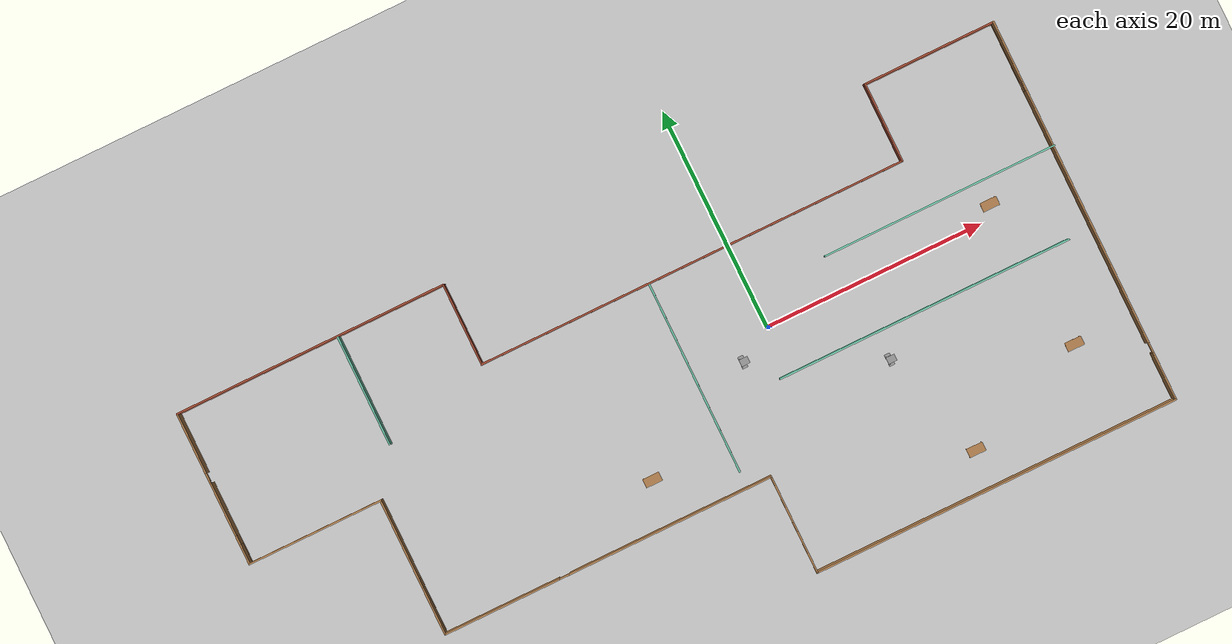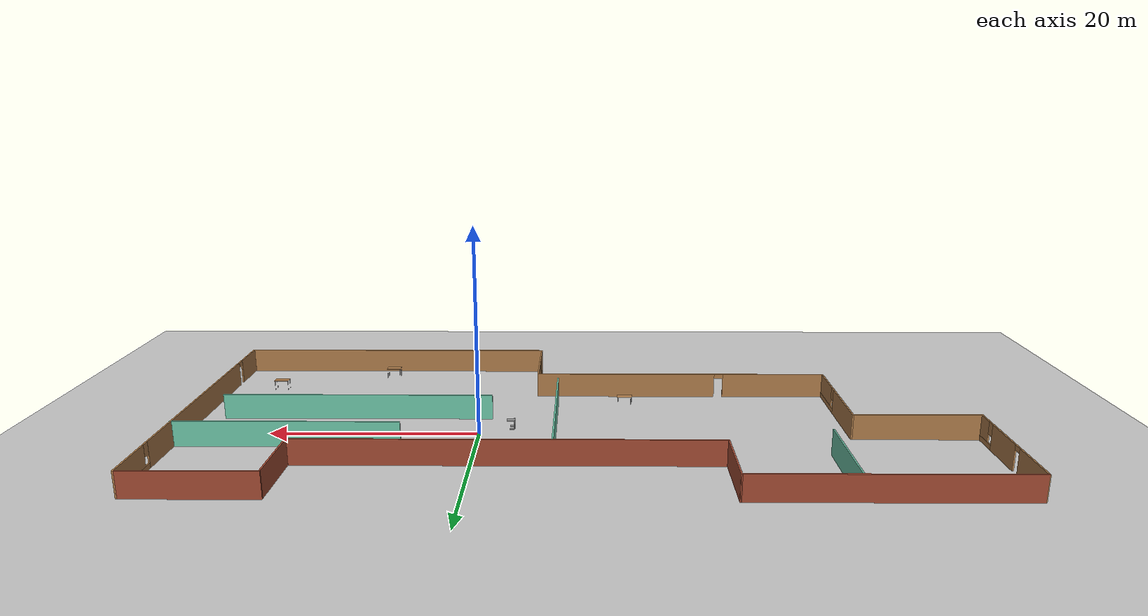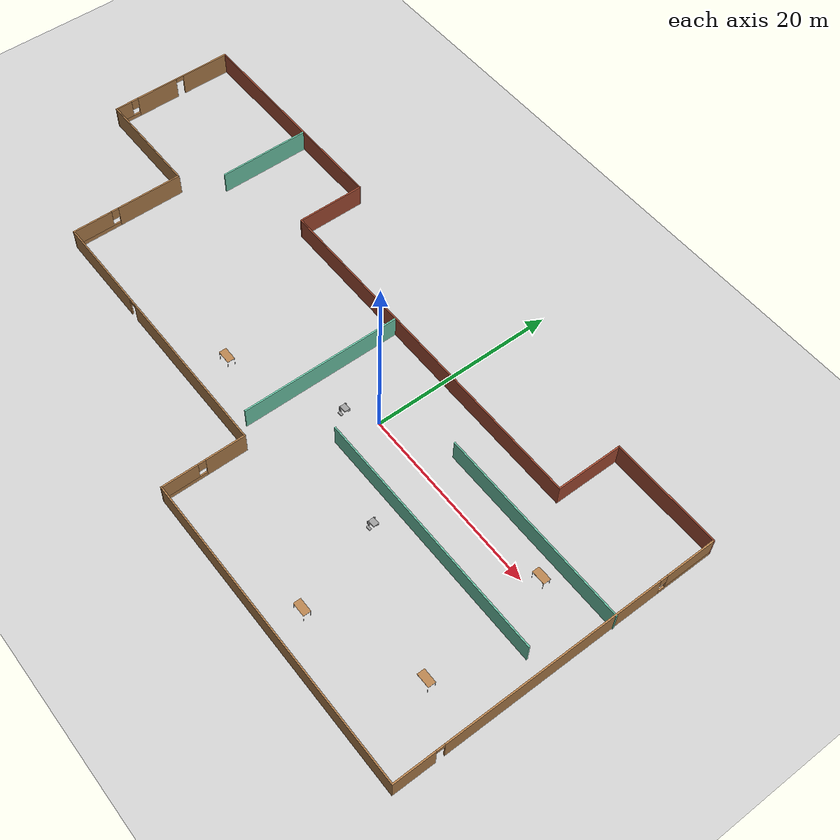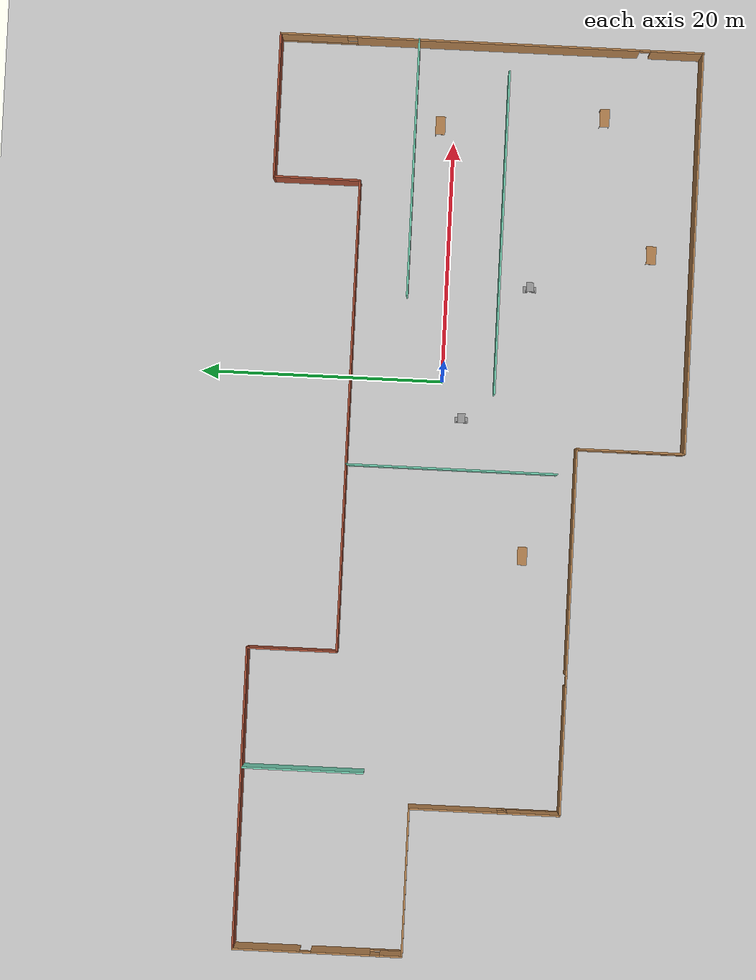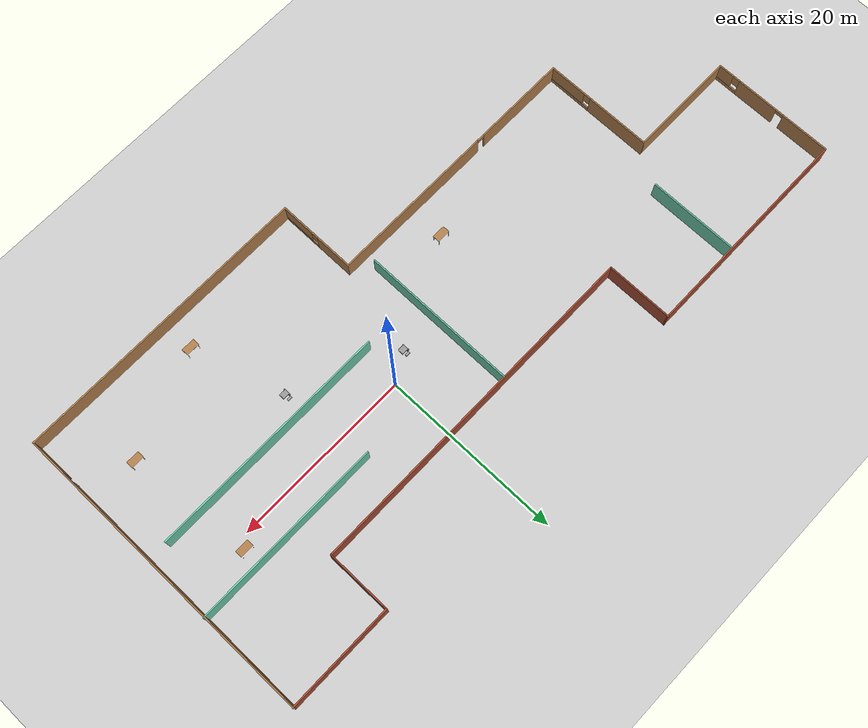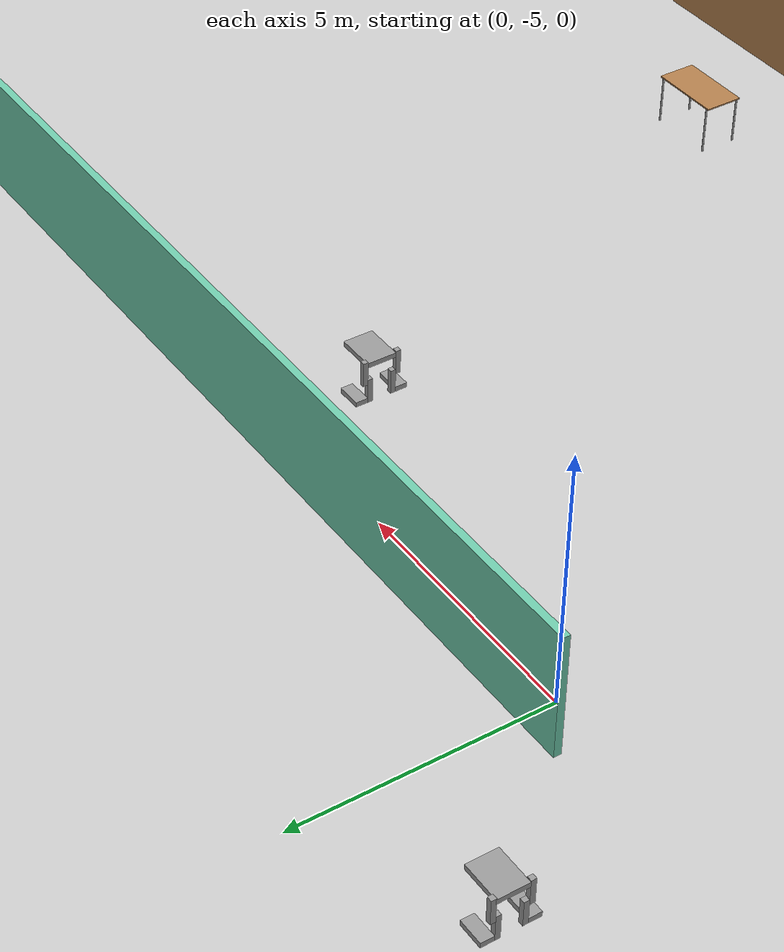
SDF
<sdf version="1.7">
 <world name="default">
  <plugin name="welcome_message" filename="libwelcome_message.so"/>
  <light name="sun" type="directional">
   <pose>0 0 10 0 -0 0</pose>
   <diffuse>0.8 0.8 0.8 1</diffuse>
   <specular>0.2 0.2 0.2 1</specular>
   <attenuation>
    <range>1000</range>
    <constant>0.9</constant>
    <linear>0.01</linear>
    <quadratic>0.001</quadratic>
   </attenuation>
   <direction>-0.5 0.1 -0.9</direction>
   <spot><inner_angle>0</inner_angle><outer_angle>0</outer_angle><falloff>0</falloff></spot>
  </light>
  <model name="ground_plane">
   <static>1</static>
   <link name="link">
    <collision name="collision">
     <geometry><plane><normal>0 0 1</normal><size>100 100</size></plane></geometry>
     <surface>
      <contact><collide_bitmask>65535</collide_bitmask></contact>
      <friction><ode><mu>100</mu><mu2>50</mu2></ode></friction>
     </surface>
    </collision>
    <visual name="visual">
     <cast_shadows>0</cast_shadows>
     <geometry><plane><normal>0 0 1</normal><size>100 100</size></plane></geometry>
     <material>
      <script><uri>file://media/materials/scripts/gazebo.material</uri><name>Gazebo/Grey</name></script>
     </material>
    </visual>
   </link>
  </model>
  <gravity>0 0 -9.8</gravity>
  <magnetic_field>6e-06 2.3e-05 -4.2e-05</magnetic_field>
  <atmosphere type="adiabatic"/>
  <physics type="ode">
   <max_step_size>0.001</max_step_size>
   <real_time_factor>1</real_time_factor>
   <real_time_update_rate>1000</real_time_update_rate>
  </physics>
  <scene><ambient>0.4 0.4 0.4 1</ambient><background>0.7 0.7 0.7 1</background><shadows>1</shadows></scene>
  <spherical_coordinates>
   <surface_model>EARTH_WGS84</surface_model>
   <latitude_deg>0</latitude_deg>
   <longitude_deg>0</longitude_deg>
   <elevation>0</elevation>
   <heading_deg>0</heading_deg>
  </spherical_coordinates>
  <model name="model">
   <pose>-9.63268 -2.63043 0 0 -0 0</pose>
   <link name="Wall_10">
    <collision name="Wall_10_Collision">
     <geometry><box><size>7.25 0.15 2.5</size></box></geometry>
     <pose>0 0 1.25 0 -0 0</pose>
    </collision>
    <visual name="Wall_10_Visual">
     <pose>0 0 1.25 0 -0 0</pose>
     <geometry><box><size>7.25 0.15 2.5</size></box></geometry>
     <material>
      <script><uri>file://media/materials/scripts/gazebo.material</uri><name>Gazebo/Bricks</name></script>
      <ambient>1 1 1 1</ambient>
     </material>
     <meta><layer>0</layer></meta>
    </visual>
    <pose>25.763 13.7499 0 0 -0 -1.5708</pose>
   </link>
   <link name="Wall_11">
    <collision name="Wall_11_Collision">
     <geometry><box><size>39 0.15 2.5</size></box></geometry>
     <pose>0 0 1.25 0 -0 0</pose>
    </collision>
    <visual name="Wall_11_Visual">
     <pose>0 0 1.25 0 -0 0</pose>
     <geometry><box><size>39 0.15 2.5</size></box></geometry>
     <material>
      <script><uri>file://media/materials/scripts/gazebo.material</uri><name>Gazebo/Bricks</name></script>
      <ambient>1 1 1 1</ambient>
     </material>
     <meta><layer>0</layer></meta>
    </visual>
    <pose>6.33798 10.1999 0 0 -0 3.14159</pose>
   </link>
   <link name="Wall_12">
    <collision name="Wall_12_Collision">
     <geometry><box><size>7.5 0.15 2.5</size></box></geometry>
     <pose>0 0 1.25 0 -0 0</pose>
    </collision>
    <visual name="Wall_12_Visual">
     <pose>0 0 1.25 0 -0 0</pose>
     <geometry><box><size>7.5 0.15 2.5</size></box></geometry>
     <material>
      <script><uri>file://media/materials/scripts/gazebo.material</uri><name>Gazebo/Bricks</name></script>
      <ambient>1 1 1 1</ambient>
     </material>
     <meta><layer>0</layer></meta>
    </visual>
    <pose>-13.087 13.8749 0 0 -0 1.5708</pose>
   </link>
   <link name="Wall_13">
    <collision name="Wall_13_Collision">
     <geometry><box><size>24.7501 0.15 2.5</size></box></geometry>
     <pose>0 0 1.25 0 -0 0</pose>
    </collision>
    <visual name="Wall_13_Visual">
     <pose>0 0 1.25 0 -0 0</pose>
     <geometry><box><size>24.7501 0.15 2.5</size></box></geometry>
     <material>
      <script><uri>file://media/materials/scripts/gazebo.material</uri><name>Gazebo/Bricks</name></script>
      <ambient>1 1 1 1</ambient>
     </material>
     <meta><layer>0</layer></meta>
    </visual>
    <pose>-25.387 17.5249 0 0 -0 -3.13956</pose>
   </link>
   <link name="Wall_15">
    <collision name="Wall_15_Collision">
     <geometry><box><size>26.75 0.15 2.5</size></box></geometry>
     <pose>0 0 1.25 0 -0 0</pose>
    </collision>
    <visual name="Wall_15_Visual">
     <pose>0 0 1.25 0 -0 0</pose>
     <geometry><box><size>26.75 0.15 2.5</size></box></geometry>
     <material>
      <script><uri>file://media/materials/scripts/gazebo.material</uri><name>Gazebo/Grey</name></script>
      <ambient>0.435294 0.796078 0.67451 1</ambient>
     </material>
     <meta><layer>0</layer></meta>
    </visual>
    <pose>22.0838 -1.70354 0 0 -0 3.14159</pose>
   </link>
   <link name="Wall_18">
    <collision name="Wall_18_Collision">
     <geometry><box><size>21.25 0.15 2.5</size></box></geometry>
     <pose>0 0 1.25 0 -0 0</pose>
    </collision>
    <visual name="Wall_18_Visual">
     <pose>0 0 1.25 0 -0 0</pose>
     <geometry><box><size>21.25 0.15 2.5</size></box></geometry>
     <material>
      <script><uri>file://media/materials/scripts/gazebo.material</uri><name>Gazebo/Grey</name></script>
      <ambient>0.435294 0.796078 0.67451 1</ambient>
     </material>
     <meta><layer>0</layer></meta>
    </visual>
    <pose>27.1372 5.86393 0 0 -0 0</pose>
   </link>
   <link name="Wall_2">
    <pose>-37.687 10.5749 0 0 -0 -1.5708</pose>
    <visual name="Wall_2_Visual_0">
     <pose>-4.21747 0 1.25 0 -0 0</pose>
     <geometry><box><size>5.56506 0.15 2.5</size></box></geometry>
     <material>
      <script><uri>file://media/materials/scripts/gazebo.material</uri><name>Gazebo/Wood</name></script>
      <ambient>1 1 1 1</ambient>
     </material>
     <meta><layer>0</layer></meta>
    </visual>
    <collision name="Wall_2_Collision_0">
     <geometry><box><size>5.56506 0.15 2.5</size></box></geometry>
     <pose>-4.21747 0 1.25 0 -0 0</pose>
    </collision>
    <visual name="Wall_2_Visual_1">
     <pose>1.88803 0 1.25 0 -0 0</pose>
     <geometry><box><size>4.84594 0.15 2.5</size></box></geometry>
     <material>
      <script><uri>file://media/materials/scripts/gazebo.material</uri><name>Gazebo/Wood</name></script>
      <ambient>1 1 1 1</ambient>
     </material>
     <meta><layer>0</layer></meta>
    </visual>
    <collision name="Wall_2_Collision_1">
     <geometry><box><size>4.84594 0.15 2.5</size></box></geometry>
     <pose>1.88803 0 1.25 0 -0 0</pose>
    </collision>
    <visual name="Wall_2_Visual_2">
     <pose>5.6555 0 0.25 0 -0 0</pose>
     <geometry><box><size>2.689 0.15 0.5</size></box></geometry>
     <material>
      <script><uri>file://media/materials/scripts/gazebo.material</uri><name>Gazebo/Wood</name></script>
      <ambient>1 1 1 1</ambient>
     </material>
     <meta><layer>0</layer></meta>
    </visual>
    <collision name="Wall_2_Collision_2">
     <geometry><box><size>2.689 0.15 0.5</size></box></geometry>
     <pose>5.6555 0 0.25 0 -0 0</pose>
    </collision>
    <visual name="Wall_2_Visual_3">
     <pose>6.0555 0 1.5 0 -0 0</pose>
     <geometry><box><size>1.889 0.15 2</size></box></geometry>
     <material>
      <script><uri>file://media/materials/scripts/gazebo.material</uri><name>Gazebo/Wood</name></script>
      <ambient>1 1 1 1</ambient>
     </material>
     <meta><layer>0</layer></meta>
    </visual>
    <collision name="Wall_2_Collision_3">
     <geometry><box><size>1.889 0.15 2</size></box></geometry>
     <pose>6.0555 0 1.5 0 -0 0</pose>
    </collision>
    <visual name="Wall_2_Visual_4">
     <pose>4.711 0 1.9 0 -0 0</pose>
     <geometry><box><size>0.8 0.15 1.2</size></box></geometry>
     <material>
      <script><uri>file://media/materials/scripts/gazebo.material</uri><name>Gazebo/Wood</name></script>
      <ambient>1 1 1 1</ambient>
     </material>
     <meta><layer>0</layer></meta>
    </visual>
    <collision name="Wall_2_Collision_4">
     <geometry><box><size>0.8 0.15 1.2</size></box></geometry>
     <pose>4.711 0 1.9 0 -0 0</pose>
    </collision>
    <visual name="Wall_2_Visual_5">
     <pose>-0.984945 0 2.25 0 -0 0</pose>
     <geometry><box><size>0.9 0.15 0.5</size></box></geometry>
     <material>
      <script><uri>file://media/materials/scripts/gazebo.material</uri><name>Gazebo/Wood</name></script>
      <ambient>1 1 1 1</ambient>
     </material>
     <meta><layer>0</layer></meta>
    </visual>
    <collision name="Wall_2_Collision_5">
     <geometry><box><size>0.9 0.15 0.5</size></box></geometry>
     <pose>-0.984945 0 2.25 0 -0 0</pose>
    </collision>
   </link>
   <link name="Wall_20">
    <collision name="Wall_20_Collision">
     <geometry><box><size>17.5 0.15 2.5</size></box></geometry>
     <pose>0 0 1.25 0 -0 0</pose>
    </collision>
    <visual name="Wall_20_Visual">
     <pose>0 0 1.25 0 -0 0</pose>
     <geometry><box><size>17.5 0.15 2.5</size></box></geometry>
     <material>
      <script><uri>file://media/materials/scripts/gazebo.material</uri><name>Gazebo/Grey</name></script>
      <ambient>0.435294 0.796078 0.67451 1</ambient>
     </material>
     <meta><layer>0</layer></meta>
    </visual>
    <pose>2.34732 1.51963 0 0 -0 1.5708</pose>
   </link>
   <link name="Wall_22">
    <collision name="Wall_22_Collision">
     <geometry><box><size>10 0.15 2.5</size></box></geometry>
     <pose>0 0 1.25 0 -0 0</pose>
    </collision>
    <visual name="Wall_22_Visual">
     <pose>0 0 1.25 0 -0 0</pose>
     <geometry><box><size>10 0.15 2.5</size></box></geometry>
     <material>
      <script><uri>file://media/materials/scripts/gazebo.material</uri><name>Gazebo/Grey</name></script>
      <ambient>0.435294 0.796078 0.67451 1</ambient>
     </material>
     <meta><layer>0</layer></meta>
    </visual>
    <pose>-22.8776 12.4936 0 0 -0 -1.5708</pose>
   </link>
   <link name="Wall_3">
    <collision name="Wall_3_Collision">
     <geometry><box><size>12.25 0.15 2.5</size></box></geometry>
     <pose>0 0 1.25 0 -0 0</pose>
    </collision>
    <visual name="Wall_3_Visual">
     <pose>0 0 1.25 0 -0 0</pose>
     <geometry><box><size>12.25 0.15 2.5</size></box></geometry>
     <material>
      <script><uri>file://media/materials/scripts/gazebo.material</uri><name>Gazebo/Wood</name></script>
      <ambient>1 1 1 1</ambient>
     </material>
     <meta><layer>0</layer></meta>
    </visual>
    <pose>-31.637 3.64993 0 0 -0 0</pose>
   </link>
   <link name="Wall_4">
    <pose>-25.587 -2.52507 0 0 -0 -1.5708</pose>
    <visual name="Wall_4_Visual_0">
     <pose>-2.59658 0 1.25 0 -0 0</pose>
     <geometry><box><size>7.30684 0.15 2.5</size></box></geometry>
     <material>
      <script><uri>file://media/materials/scripts/gazebo.material</uri><name>Gazebo/Wood</name></script>
      <ambient>1 1 1 1</ambient>
     </material>
     <meta><layer>0</layer></meta>
    </visual>
    <collision name="Wall_4_Collision_0">
     <geometry><box><size>7.30684 0.15 2.5</size></box></geometry>
     <pose>-2.59658 0 1.25 0 -0 0</pose>
    </collision>
    <visual name="Wall_4_Visual_1">
     <pose>3.65342 0 0.25 0 -0 0</pose>
     <geometry><box><size>5.19316 0.15 0.5</size></box></geometry>
     <material>
      <script><uri>file://media/materials/scripts/gazebo.material</uri><name>Gazebo/Wood</name></script>
      <ambient>1 1 1 1</ambient>
     </material>
     <meta><layer>0</layer></meta>
    </visual>
    <collision name="Wall_4_Collision_1">
     <geometry><box><size>5.19316 0.15 0.5</size></box></geometry>
     <pose>3.65342 0 0.25 0 -0 0</pose>
    </collision>
    <visual name="Wall_4_Visual_2">
     <pose>4.05342 0 1.5 0 -0 0</pose>
     <geometry><box><size>4.39316 0.15 2</size></box></geometry>
     <material>
      <script><uri>file://media/materials/scripts/gazebo.material</uri><name>Gazebo/Wood</name></script>
      <ambient>1 1 1 1</ambient>
     </material>
     <meta><layer>0</layer></meta>
    </visual>
    <collision name="Wall_4_Collision_2">
     <geometry><box><size>4.39316 0.15 2</size></box></geometry>
     <pose>4.05342 0 1.5 0 -0 0</pose>
    </collision>
    <visual name="Wall_4_Visual_3">
     <pose>1.45684 0 1.9 0 -0 0</pose>
     <geometry><box><size>0.8 0.15 1.2</size></box></geometry>
     <material>
      <script><uri>file://media/materials/scripts/gazebo.material</uri><name>Gazebo/Wood</name></script>
      <ambient>1 1 1 1</ambient>
     </material>
     <meta><layer>0</layer></meta>
    </visual>
    <collision name="Wall_4_Collision_3">
     <geometry><box><size>0.8 0.15 1.2</size></box></geometry>
     <pose>1.45684 0 1.9 0 -0 0</pose>
    </collision>
   </link>
   <link name="Wall_5">
    <pose>-10.537 -8.70007 0 0 -0 0</pose>
    <visual name="Wall_5_Visual_0">
     <pose>-9.80787 0 1.25 0 -0 0</pose>
     <geometry><box><size>10.6343 0.15 2.5</size></box></geometry>
     <material>
      <script><uri>file://media/materials/scripts/gazebo.material</uri><name>Gazebo/Wood</name></script>
      <ambient>1 1 1 1</ambient>
     </material>
     <meta><layer>0</layer></meta>
    </visual>
    <collision name="Wall_5_Collision_0">
     <geometry><box><size>10.6343 0.15 2.5</size></box></geometry>
     <pose>-9.80787 0 1.25 0 -0 0</pose>
    </collision>
    <visual name="Wall_5_Visual_1">
     <pose>5.76713 0 1.25 0 -0 0</pose>
     <geometry><box><size>18.7157 0.15 2.5</size></box></geometry>
     <material>
      <script><uri>file://media/materials/scripts/gazebo.material</uri><name>Gazebo/Wood</name></script>
      <ambient>1 1 1 1</ambient>
     </material>
     <meta><layer>0</layer></meta>
    </visual>
    <collision name="Wall_5_Collision_1">
     <geometry><box><size>18.7157 0.15 2.5</size></box></geometry>
     <pose>5.76713 0 1.25 0 -0 0</pose>
    </collision>
    <visual name="Wall_5_Visual_2">
     <pose>-4.04075 0 2.25 0 -0 0</pose>
     <geometry><box><size>0.9 0.15 0.5</size></box></geometry>
     <material>
      <script><uri>file://media/materials/scripts/gazebo.material</uri><name>Gazebo/Wood</name></script>
      <ambient>1 1 1 1</ambient>
     </material>
     <meta><layer>0</layer></meta>
    </visual>
    <collision name="Wall_5_Collision_2">
     <geometry><box><size>0.9 0.15 0.5</size></box></geometry>
     <pose>-4.04075 0 2.25 0 -0 0</pose>
    </collision>
   </link>
   <link name="Wall_6">
    <pose>4.51298 -13.1251 0 0 -0 -1.5708</pose>
    <visual name="Wall_6_Visual_0">
     <pose>-2.34277 0 1.25 0 -0 0</pose>
     <geometry><box><size>4.31446 0.15 2.5</size></box></geometry>
     <material>
      <script><uri>file://media/materials/scripts/gazebo.material</uri><name>Gazebo/Wood</name></script>
      <ambient>1 1 1 1</ambient>
     </material>
     <meta><layer>0</layer></meta>
    </visual>
    <collision name="Wall_6_Collision_0">
     <geometry><box><size>4.31446 0.15 2.5</size></box></geometry>
     <pose>-2.34277 0 1.25 0 -0 0</pose>
    </collision>
    <visual name="Wall_6_Visual_1">
     <pose>2.15723 0 0.25 0 -0 0</pose>
     <geometry><box><size>4.68554 0.15 0.5</size></box></geometry>
     <material>
      <script><uri>file://media/materials/scripts/gazebo.material</uri><name>Gazebo/Wood</name></script>
      <ambient>1 1 1 1</ambient>
     </material>
     <meta><layer>0</layer></meta>
    </visual>
    <collision name="Wall_6_Collision_1">
     <geometry><box><size>4.68554 0.15 0.5</size></box></geometry>
     <pose>2.15723 0 0.25 0 -0 0</pose>
    </collision>
    <visual name="Wall_6_Visual_2">
     <pose>2.55723 0 1.5 0 -0 0</pose>
     <geometry><box><size>3.88554 0.15 2</size></box></geometry>
     <material>
      <script><uri>file://media/materials/scripts/gazebo.material</uri><name>Gazebo/Wood</name></script>
      <ambient>1 1 1 1</ambient>
     </material>
     <meta><layer>0</layer></meta>
    </visual>
    <collision name="Wall_6_Collision_2">
     <geometry><box><size>3.88554 0.15 2</size></box></geometry>
     <pose>2.55723 0 1.5 0 -0 0</pose>
    </collision>
    <visual name="Wall_6_Visual_3">
     <pose>0.214463 0 1.9 0 -0 0</pose>
     <geometry><box><size>0.8 0.15 1.2</size></box></geometry>
     <material>
      <script><uri>file://media/materials/scripts/gazebo.material</uri><name>Gazebo/Wood</name></script>
      <ambient>1 1 1 1</ambient>
     </material>
     <meta><layer>0</layer></meta>
    </visual>
    <collision name="Wall_6_Collision_3">
     <geometry><box><size>0.8 0.15 1.2</size></box></geometry>
     <pose>0.214463 0 1.9 0 -0 0</pose>
    </collision>
   </link>
   <link name="Wall_7">
    <collision name="Wall_7_Collision">
     <geometry><box><size>33.25 0.15 2.5</size></box></geometry>
     <pose>0 0 1.25 0 -0 0</pose>
    </collision>
    <visual name="Wall_7_Visual">
     <pose>0 0 1.25 0 -0 0</pose>
     <geometry><box><size>33.25 0.15 2.5</size></box></geometry>
     <material>
      <script><uri>file://media/materials/scripts/gazebo.material</uri><name>Gazebo/Wood</name></script>
      <ambient>1 1 1 1</ambient>
     </material>
     <meta><layer>0</layer></meta>
    </visual>
    <pose>21.063 -17.5501 0 0 -0 0</pose>
   </link>
   <link name="Wall_8">
    <pose>37.613 -0.125074 0 0 -0 1.5708</pose>
    <visual name="Wall_8_Visual_0">
     <pose>-15.2974 0 1.25 0 -0 0</pose>
     <geometry><box><size>4.40513 0.15 2.5</size></box></geometry>
     <material>
      <script><uri>file://media/materials/scripts/gazebo.material</uri><name>Gazebo/Wood</name></script>
      <ambient>1 1 1 1</ambient>
     </material>
     <meta><layer>0</layer></meta>
    </visual>
    <collision name="Wall_8_Collision_0">
     <geometry><box><size>4.40513 0.15 2.5</size></box></geometry>
     <pose>-15.2974 0 1.25 0 -0 0</pose>
    </collision>
    <visual name="Wall_8_Visual_1">
     <pose>-0.536333 0 1.25 0 -0 0</pose>
     <geometry><box><size>23.3171 0.15 2.5</size></box></geometry>
     <material>
      <script><uri>file://media/materials/scripts/gazebo.material</uri><name>Gazebo/Wood</name></script>
      <ambient>1 1 1 1</ambient>
     </material>
     <meta><layer>0</layer></meta>
    </visual>
    <collision name="Wall_8_Collision_1">
     <geometry><box><size>23.3171 0.15 2.5</size></box></geometry>
     <pose>-0.536333 0 1.25 0 -0 0</pose>
    </collision>
    <visual name="Wall_8_Visual_2">
     <pose>14.3111 0 0.25 0 -0 0</pose>
     <geometry><box><size>6.3778 0.15 0.5</size></box></geometry>
     <material>
      <script><uri>file://media/materials/scripts/gazebo.material</uri><name>Gazebo/Wood</name></script>
      <ambient>1 1 1 1</ambient>
     </material>
     <meta><layer>0</layer></meta>
    </visual>
    <collision name="Wall_8_Collision_2">
     <geometry><box><size>6.3778 0.15 0.5</size></box></geometry>
     <pose>14.3111 0 0.25 0 -0 0</pose>
    </collision>
    <visual name="Wall_8_Visual_3">
     <pose>14.7111 0 1.5 0 -0 0</pose>
     <geometry><box><size>5.5778 0.15 2</size></box></geometry>
     <material>
      <script><uri>file://media/materials/scripts/gazebo.material</uri><name>Gazebo/Wood</name></script>
      <ambient>1 1 1 1</ambient>
     </material>
     <meta><layer>0</layer></meta>
    </visual>
    <collision name="Wall_8_Collision_3">
     <geometry><box><size>5.5778 0.15 2</size></box></geometry>
     <pose>14.7111 0 1.5 0 -0 0</pose>
    </collision>
    <visual name="Wall_8_Visual_4">
     <pose>11.5222 0 1.9 0 -0 0</pose>
     <geometry><box><size>0.8 0.15 1.2</size></box></geometry>
     <material>
      <script><uri>file://media/materials/scripts/gazebo.material</uri><name>Gazebo/Wood</name></script>
      <ambient>1 1 1 1</ambient>
     </material>
     <meta><layer>0</layer></meta>
    </visual>
    <collision name="Wall_8_Collision_4">
     <geometry><box><size>0.8 0.15 1.2</size></box></geometry>
     <pose>11.5222 0 1.9 0 -0 0</pose>
    </collision>
    <visual name="Wall_8_Visual_5">
     <pose>-12.6449 0 2.25 0 -0 0</pose>
     <geometry><box><size>0.9 0.15 0.5</size></box></geometry>
     <material>
      <script><uri>file://media/materials/scripts/gazebo.material</uri><name>Gazebo/Wood</name></script>
      <ambient>1 1 1 1</ambient>
     </material>
     <meta><layer>0</layer></meta>
    </visual>
    <collision name="Wall_8_Collision_5">
     <geometry><box><size>0.9 0.15 0.5</size></box></geometry>
     <pose>-12.6449 0 2.25 0 -0 0</pose>
    </collision>
   </link>
   <link name="Wall_9">
    <collision name="Wall_9_Collision">
     <geometry><box><size>12 0.15 2.5</size></box></geometry>
     <pose>0 0 1.25 0 -0 0</pose>
    </collision>
    <visual name="Wall_9_Visual">
     <pose>0 0 1.25 0 -0 0</pose>
     <geometry><box><size>12 0.15 2.5</size></box></geometry>
     <material>
      <script><uri>file://media/materials/scripts/gazebo.material</uri><name>Gazebo/Bricks</name></script>
      <ambient>1 1 1 1</ambient>
     </material>
     <meta><layer>0</layer></meta>
    </visual>
    <pose>31.688 17.2999 0 0 -0 3.14159</pose>
   </link>
   <static>1</static>
  </model>
  <model name="model_0">
   <link name="link_0">
    <inertial>
     <mass>1</mass>
     <inertia>
      <ixx>0.166667</ixx>
      <ixy>0</ixy>
      <ixz>0</ixz>
      <iyy>0.166667</iyy>
      <iyz>0</iyz>
      <izz>0.166667</izz>
     </inertia>
    </inertial>
    <pose>8.2677 -7.12192 0.05 0 -0 0</pose>
    <visual name="visual">
     <geometry><box><size>0.5 0.25 0.1</size></box></geometry>
     <material>
      <lighting>1</lighting>
      <script><uri>file://media/materials/scripts/gazebo.material</uri><name>Gazebo/Grey</name></script>
      <shader type="pixel"><normal_map>__default__</normal_map></shader>
      <ambient>0.3 0.3 0.3 1</ambient>
      <diffuse>0.7 0.7 0.7 1</diffuse>
      <specular>0.01 0.01 0.01 1</specular>
      <emissive>0 0 0 1</emissive>
     </material>
    </visual>
    <collision name="collision">
     <geometry><box><size>0.5 0.25 0.1</size></box></geometry>
     <surface>
      <friction>
       <ode><mu>1</mu><mu2>1</mu2><fdir1>0 0 0</fdir1><slip1>0</slip1><slip2>0</slip2></ode>
       <torsional>
        <coefficient>1</coefficient>
        <patch_radius>0</patch_radius>
        <surface_radius>0</surface_radius>
        <use_patch_radius>1</use_patch_radius>
        <ode><slip>0</slip></ode>
       </torsional>
      </friction>
      <bounce><restitution_coefficient>0</restitution_coefficient><threshold>1e+06</threshold></bounce>
      <contact>
       <collide_without_contact>0</collide_without_contact>
       <collide_without_contact_bitmask>1</collide_without_contact_bitmask>
       <collide_bitmask>1</collide_bitmask>
       <ode>
        <soft_cfm>0</soft_cfm>
        <soft_erp>0.2</soft_erp>
        <kp>1e+13</kp>
        <kd>1</kd>
        <max_vel>0.01</max_vel>
        <min_depth>0</min_depth>
       </ode>
       <bullet>
        <split_impulse>1</split_impulse>
        <split_impulse_penetration_threshold>-0.01</split_impulse_penetration_threshold>
        <soft_cfm>0</soft_cfm>
        <soft_erp>0.2</soft_erp>
        <kp>1e+13</kp>
        <kd>1</kd>
       </bullet>
      </contact>
     </surface>
    </collision>
   </link>
   <link name="link_0_clone">
    <inertial>
     <mass>1</mass>
     <inertia>
      <ixx>0.166667</ixx>
      <ixy>0</ixy>
      <ixz>0</ixz>
      <iyy>0.166667</iyy>
      <iyz>0</iyz>
      <izz>0.166667</izz>
     </inertia>
    </inertial>
    <pose>8.2677 -6.28909 0.05 0 -0 0</pose>
    <visual name="visual">
     <geometry><box><size>0.5 0.25 0.1</size></box></geometry>
     <material>
      <lighting>1</lighting>
      <script><uri>file://media/materials/scripts/gazebo.material</uri><name>Gazebo/Grey</name></script>
      <shader type="pixel"><normal_map>__default__</normal_map></shader>
      <ambient>0.3 0.3 0.3 1</ambient>
      <diffuse>0.7 0.7 0.7 1</diffuse>
      <specular>0.01 0.01 0.01 1</specular>
      <emissive>0 0 0 1</emissive>
     </material>
    </visual>
    <collision name="collision">
     <geometry><box><size>0.5 0.25 0.1</size></box></geometry>
     <surface>
      <friction>
       <ode><mu>1</mu><mu2>1</mu2><fdir1>0 0 0</fdir1><slip1>0</slip1><slip2>0</slip2></ode>
       <torsional>
        <coefficient>1</coefficient>
        <patch_radius>0</patch_radius>
        <surface_radius>0</surface_radius>
        <use_patch_radius>1</use_patch_radius>
        <ode><slip>0</slip></ode>
       </torsional>
      </friction>
      <bounce><restitution_coefficient>0</restitution_coefficient><threshold>1e+06</threshold></bounce>
      <contact>
       <collide_without_contact>0</collide_without_contact>
       <collide_without_contact_bitmask>1</collide_without_contact_bitmask>
       <collide_bitmask>1</collide_bitmask>
       <ode>
        <soft_cfm>0</soft_cfm>
        <soft_erp>0.2</soft_erp>
        <kp>1e+13</kp>
        <kd>1</kd>
        <max_vel>0.01</max_vel>
        <min_depth>0</min_depth>
       </ode>
       <bullet>
        <split_impulse>1</split_impulse>
        <split_impulse_penetration_threshold>-0.01</split_impulse_penetration_threshold>
        <soft_cfm>0</soft_cfm>
        <soft_erp>0.2</soft_erp>
        <kp>1e+13</kp>
        <kd>1</kd>
       </bullet>
      </contact>
     </surface>
    </collision>
   </link>
   <link name="link_1">
    <inertial>
     <mass>1</mass>
     <inertia>
      <ixx>0.166667</ixx>
      <ixy>0</ixy>
      <ixz>0</ixz>
      <iyy>0.166667</iyy>
      <iyz>0</iyz>
      <izz>0.166667</izz>
     </inertia>
    </inertial>
    <pose>8.0677 -6.95104 0.25 0 -0 0</pose>
    <visual name="visual">
     <geometry><box><size>0.1 0.1 0.5</size></box></geometry>
     <material>
      <lighting>1</lighting>
      <script><uri>file://media/materials/scripts/gazebo.material</uri><name>Gazebo/Grey</name></script>
      <shader type="pixel"><normal_map>__default__</normal_map></shader>
      <ambient>0.3 0.3 0.3 1</ambient>
      <diffuse>0.7 0.7 0.7 1</diffuse>
      <specular>0.01 0.01 0.01 1</specular>
      <emissive>0 0 0 1</emissive>
     </material>
    </visual>
    <collision name="collision">
     <geometry><box><size>0.1 0.1 0.5</size></box></geometry>
     <surface>
      <friction>
       <ode><mu>1</mu><mu2>1</mu2><fdir1>0 0 0</fdir1><slip1>0</slip1><slip2>0</slip2></ode>
       <torsional>
        <coefficient>1</coefficient>
        <patch_radius>0</patch_radius>
        <surface_radius>0</surface_radius>
        <use_patch_radius>1</use_patch_radius>
        <ode><slip>0</slip></ode>
       </torsional>
      </friction>
      <bounce><restitution_coefficient>0</restitution_coefficient><threshold>1e+06</threshold></bounce>
      <contact>
       <collide_without_contact>0</collide_without_contact>
       <collide_without_contact_bitmask>1</collide_without_contact_bitmask>
       <collide_bitmask>1</collide_bitmask>
       <ode>
        <soft_cfm>0</soft_cfm>
        <soft_erp>0.2</soft_erp>
        <kp>1e+13</kp>
        <kd>1</kd>
        <max_vel>0.01</max_vel>
        <min_depth>0</min_depth>
       </ode>
       <bullet>
        <split_impulse>1</split_impulse>
        <split_impulse_penetration_threshold>-0.01</split_impulse_penetration_threshold>
        <soft_cfm>0</soft_cfm>
        <soft_erp>0.2</soft_erp>
        <kp>1e+13</kp>
        <kd>1</kd>
       </bullet>
      </contact>
     </surface>
    </collision>
   </link>
   <link name="link_1_clone">
    <inertial>
     <mass>1</mass>
     <inertia>
      <ixx>0.166667</ixx>
      <ixy>0</ixy>
      <ixz>0</ixz>
      <iyy>0.166667</iyy>
      <iyz>0</iyz>
      <izz>0.166667</izz>
     </inertia>
    </inertial>
    <pose>8.0677 -6.46409 0.25 0 -0 0</pose>
    <visual name="visual">
     <geometry><box><size>0.1 0.1 0.5</size></box></geometry>
     <material>
      <lighting>1</lighting>
      <script><uri>file://media/materials/scripts/gazebo.material</uri><name>Gazebo/Grey</name></script>
      <shader type="pixel"><normal_map>__default__</normal_map></shader>
      <ambient>0.3 0.3 0.3 1</ambient>
      <diffuse>0.7 0.7 0.7 1</diffuse>
      <specular>0.01 0.01 0.01 1</specular>
      <emissive>0 0 0 1</emissive>
     </material>
    </visual>
    <collision name="collision">
     <geometry><box><size>0.1 0.1 0.5</size></box></geometry>
     <surface>
      <friction>
       <ode><mu>1</mu><mu2>1</mu2><fdir1>0 0 0</fdir1><slip1>0</slip1><slip2>0</slip2></ode>
       <torsional>
        <coefficient>1</coefficient>
        <patch_radius>0</patch_radius>
        <surface_radius>0</surface_radius>
        <use_patch_radius>1</use_patch_radius>
        <ode><slip>0</slip></ode>
       </torsional>
      </friction>
      <bounce><restitution_coefficient>0</restitution_coefficient><threshold>1e+06</threshold></bounce>
      <contact>
       <collide_without_contact>0</collide_without_contact>
       <collide_without_contact_bitmask>1</collide_without_contact_bitmask>
       <collide_bitmask>1</collide_bitmask>
       <ode>
        <soft_cfm>0</soft_cfm>
        <soft_erp>0.2</soft_erp>
        <kp>1e+13</kp>
        <kd>1</kd>
        <max_vel>0.01</max_vel>
        <min_depth>0</min_depth>
       </ode>
       <bullet>
        <split_impulse>1</split_impulse>
        <split_impulse_penetration_threshold>-0.01</split_impulse_penetration_threshold>
        <soft_cfm>0</soft_cfm>
        <soft_erp>0.2</soft_erp>
        <kp>1e+13</kp>
        <kd>1</kd>
       </bullet>
      </contact>
     </surface>
    </collision>
   </link>
   <link name="link_1_clone_0">
    <inertial>
     <mass>1</mass>
     <inertia>
      <ixx>0.166667</ixx>
      <ixy>0</ixy>
      <ixz>0</ixz>
      <iyy>0.166667</iyy>
      <iyz>0</iyz>
      <izz>0.166667</izz>
     </inertia>
    </inertial>
    <pose>8.0677 -7.05104 0.65 0 -0 0</pose>
    <visual name="visual">
     <geometry><box><size>0.1 0.1 0.5</size></box></geometry>
     <material>
      <lighting>1</lighting>
      <script><uri>file://media/materials/scripts/gazebo.material</uri><name>Gazebo/Grey</name></script>
      <shader type="pixel"><normal_map>__default__</normal_map></shader>
      <ambient>0.3 0.3 0.3 1</ambient>
      <diffuse>0.7 0.7 0.7 1</diffuse>
      <specular>0.01 0.01 0.01 1</specular>
      <emissive>0 0 0 1</emissive>
     </material>
    </visual>
    <collision name="collision">
     <geometry><box><size>0.1 0.1 0.5</size></box></geometry>
     <surface>
      <friction>
       <ode><mu>1</mu><mu2>1</mu2><fdir1>0 0 0</fdir1><slip1>0</slip1><slip2>0</slip2></ode>
       <torsional>
        <coefficient>1</coefficient>
        <patch_radius>0</patch_radius>
        <surface_radius>0</surface_radius>
        <use_patch_radius>1</use_patch_radius>
        <ode><slip>0</slip></ode>
       </torsional>
      </friction>
      <bounce><restitution_coefficient>0</restitution_coefficient><threshold>1e+06</threshold></bounce>
      <contact>
       <collide_without_contact>0</collide_without_contact>
       <collide_without_contact_bitmask>1</collide_without_contact_bitmask>
       <collide_bitmask>1</collide_bitmask>
       <ode>
        <soft_cfm>0</soft_cfm>
        <soft_erp>0.2</soft_erp>
        <kp>1e+13</kp>
        <kd>1</kd>
        <max_vel>0.01</max_vel>
        <min_depth>0</min_depth>
       </ode>
       <bullet>
        <split_impulse>1</split_impulse>
        <split_impulse_penetration_threshold>-0.01</split_impulse_penetration_threshold>
        <soft_cfm>0</soft_cfm>
        <soft_erp>0.2</soft_erp>
        <kp>1e+13</kp>
        <kd>1</kd>
       </bullet>
      </contact>
     </surface>
    </collision>
   </link>
   <link name="link_1_clone_1">
    <inertial>
     <mass>1</mass>
     <inertia>
      <ixx>0.166667</ixx>
      <ixy>0</ixy>
      <ixz>0</ixz>
      <iyy>0.166667</iyy>
      <iyz>0</iyz>
      <izz>0.166667</izz>
     </inertia>
    </inertial>
    <pose>8.0677 -6.36409 0.65 0 -0 0</pose>
    <visual name="visual">
     <geometry><box><size>0.1 0.1 0.5</size></box></geometry>
     <material>
      <lighting>1</lighting>
      <script><uri>file://media/materials/scripts/gazebo.material</uri><name>Gazebo/Grey</name></script>
      <shader type="pixel"><normal_map>__default__</normal_map></shader>
      <ambient>0.3 0.3 0.3 1</ambient>
      <diffuse>0.7 0.7 0.7 1</diffuse>
      <specular>0.01 0.01 0.01 1</specular>
      <emissive>0 0 0 1</emissive>
     </material>
    </visual>
    <collision name="collision">
     <geometry><box><size>0.1 0.1 0.5</size></box></geometry>
     <surface>
      <friction>
       <ode><mu>1</mu><mu2>1</mu2><fdir1>0 0 0</fdir1><slip1>0</slip1><slip2>0</slip2></ode>
       <torsional>
        <coefficient>1</coefficient>
        <patch_radius>0</patch_radius>
        <surface_radius>0</surface_radius>
        <use_patch_radius>1</use_patch_radius>
        <ode><slip>0</slip></ode>
       </torsional>
      </friction>
      <bounce><restitution_coefficient>0</restitution_coefficient><threshold>1e+06</threshold></bounce>
      <contact>
       <collide_without_contact>0</collide_without_contact>
       <collide_without_contact_bitmask>1</collide_without_contact_bitmask>
       <collide_bitmask>1</collide_bitmask>
       <ode>
        <soft_cfm>0</soft_cfm>
        <soft_erp>0.2</soft_erp>
        <kp>1e+13</kp>
        <kd>1</kd>
        <max_vel>0.01</max_vel>
        <min_depth>0</min_depth>
       </ode>
       <bullet>
        <split_impulse>1</split_impulse>
        <split_impulse_penetration_threshold>-0.01</split_impulse_penetration_threshold>
        <soft_cfm>0</soft_cfm>
        <soft_erp>0.2</soft_erp>
        <kp>1e+13</kp>
        <kd>1</kd>
       </bullet>
      </contact>
     </surface>
    </collision>
   </link>
   <link name="link_2">
    <inertial>
     <mass>0.465511</mass>
     <inertia>
      <ixx>0.0143902</ixx>
      <ixy>0</ixy>
      <ixz>0</ixz>
      <iyy>0.0236755</iyy>
      <iyz>0</iyz>
      <izz>0.0372898</izz>
     </inertia>
    </inertial>
    <pose>8.4051 -6.70064 0.824557 0 -0 0</pose>
    <visual name="visual">
     <geometry><box><size>0.774797 0.600792 0.1</size></box></geometry>
     <material>
      <lighting>1</lighting>
      <script><uri>file://media/materials/scripts/gazebo.material</uri><name>Gazebo/Grey</name></script>
      <shader type="pixel"><normal_map>__default__</normal_map></shader>
      <ambient>0.3 0.3 0.3 1</ambient>
      <diffuse>0.7 0.7 0.7 1</diffuse>
      <specular>0.01 0.01 0.01 1</specular>
      <emissive>0 0 0 1</emissive>
     </material>
    </visual>
    <collision name="collision">
     <geometry><box><size>0.774797 0.600792 0.1</size></box></geometry>
     <surface>
      <friction>
       <ode><mu>1</mu><mu2>1</mu2><fdir1>0 0 0</fdir1><slip1>0</slip1><slip2>0</slip2></ode>
       <torsional>
        <coefficient>1</coefficient>
        <patch_radius>0</patch_radius>
        <surface_radius>0</surface_radius>
        <use_patch_radius>1</use_patch_radius>
        <ode><slip>0</slip></ode>
       </torsional>
      </friction>
      <bounce><restitution_coefficient>0</restitution_coefficient><threshold>1e+06</threshold></bounce>
      <contact>
       <collide_without_contact>0</collide_without_contact>
       <collide_without_contact_bitmask>1</collide_without_contact_bitmask>
       <collide_bitmask>1</collide_bitmask>
       <ode>
        <soft_cfm>0</soft_cfm>
        <soft_erp>0.2</soft_erp>
        <kp>1e+13</kp>
        <kd>1</kd>
        <max_vel>0.01</max_vel>
        <min_depth>0</min_depth>
       </ode>
       <bullet>
        <split_impulse>1</split_impulse>
        <split_impulse_penetration_threshold>-0.01</split_impulse_penetration_threshold>
        <soft_cfm>0</soft_cfm>
        <soft_erp>0.2</soft_erp>
        <kp>1e+13</kp>
        <kd>1</kd>
       </bullet>
      </contact>
     </surface>
    </collision>
   </link>
   <model name="model">
    <link name="link_0">
     <inertial>
      <mass>1</mass>
      <inertia>
       <ixx>0.166667</ixx>
       <ixy>0</ixy>
       <ixz>0</ixz>
       <iyy>0.166667</iyy>
       <iyz>0</iyz>
       <izz>0.166667</izz>
      </inertia>
     </inertial>
     <pose>0.094657 -0.415933 -0.339222 0 -0 0</pose>
     <visual name="visual">
      <geometry><box><size>0.5 0.25 0.1</size></box></geometry>
      <material>
       <lighting>1</lighting>
       <script><uri>file://media/materials/scripts/gazebo.material</uri><name>Gazebo/Grey</name></script>
       <shader type="pixel"><normal_map>__default__</normal_map></shader>
       <ambient>0.3 0.3 0.3 1</ambient>
       <diffuse>0.7 0.7 0.7 1</diffuse>
       <specular>0.01 0.01 0.01 1</specular>
       <emissive>0 0 0 1</emissive>
      </material>
     </visual>
     <collision name="collision">
      <geometry><box><size>0.5 0.25 0.1</size></box></geometry>
      <surface>
       <friction>
        <ode><mu>1</mu><mu2>1</mu2><fdir1>0 0 0</fdir1><slip1>0</slip1><slip2>0</slip2></ode>
        <torsional>
         <coefficient>1</coefficient>
         <patch_radius>0</patch_radius>
         <surface_radius>0</surface_radius>
         <use_patch_radius>1</use_patch_radius>
         <ode><slip>0</slip></ode>
        </torsional>
       </friction>
       <bounce><restitution_coefficient>0</restitution_coefficient><threshold>1e+06</threshold></bounce>
       <contact>
        <collide_without_contact>0</collide_without_contact>
        <collide_without_contact_bitmask>1</collide_without_contact_bitmask>
        <collide_bitmask>1</collide_bitmask>
        <ode>
         <soft_cfm>0</soft_cfm>
         <soft_erp>0.2</soft_erp>
         <kp>1e+13</kp>
         <kd>1</kd>
         <max_vel>0.01</max_vel>
         <min_depth>0</min_depth>
        </ode>
        <bullet>
         <split_impulse>1</split_impulse>
         <split_impulse_penetration_threshold>-0.01</split_impulse_penetration_threshold>
         <soft_cfm>0</soft_cfm>
         <soft_erp>0.2</soft_erp>
         <kp>1e+13</kp>
         <kd>1</kd>
        </bullet>
       </contact>
      </surface>
     </collision>
    </link>
    <link name="link_0_clone">
     <inertial>
      <mass>1</mass>
      <inertia>
       <ixx>0.166667</ixx>
       <ixy>0</ixy>
       <ixz>0</ixz>
       <iyy>0.166667</iyy>
       <iyz>0</iyz>
       <izz>0.166667</izz>
      </inertia>
     </inertial>
     <pose>0.094657 0.416897 -0.339222 0 -0 0</pose>
     <visual name="visual">
      <geometry><box><size>0.5 0.25 0.1</size></box></geometry>
      <material>
       <lighting>1</lighting>
       <script><uri>file://media/materials/scripts/gazebo.material</uri><name>Gazebo/Grey</name></script>
       <shader type="pixel"><normal_map>__default__</normal_map></shader>
       <ambient>0.3 0.3 0.3 1</ambient>
       <diffuse>0.7 0.7 0.7 1</diffuse>
       <specular>0.01 0.01 0.01 1</specular>
       <emissive>0 0 0 1</emissive>
      </material>
     </visual>
     <collision name="collision">
      <geometry><box><size>0.5 0.25 0.1</size></box></geometry>
      <surface>
       <friction>
        <ode><mu>1</mu><mu2>1</mu2><fdir1>0 0 0</fdir1><slip1>0</slip1><slip2>0</slip2></ode>
        <torsional>
         <coefficient>1</coefficient>
         <patch_radius>0</patch_radius>
         <surface_radius>0</surface_radius>
         <use_patch_radius>1</use_patch_radius>
         <ode><slip>0</slip></ode>
        </torsional>
       </friction>
       <bounce><restitution_coefficient>0</restitution_coefficient><threshold>1e+06</threshold></bounce>
       <contact>
        <collide_without_contact>0</collide_without_contact>
        <collide_without_contact_bitmask>1</collide_without_contact_bitmask>
        <collide_bitmask>1</collide_bitmask>
        <ode>
         <soft_cfm>0</soft_cfm>
         <soft_erp>0.2</soft_erp>
         <kp>1e+13</kp>
         <kd>1</kd>
         <max_vel>0.01</max_vel>
         <min_depth>0</min_depth>
        </ode>
        <bullet>
         <split_impulse>1</split_impulse>
         <split_impulse_penetration_threshold>-0.01</split_impulse_penetration_threshold>
         <soft_cfm>0</soft_cfm>
         <soft_erp>0.2</soft_erp>
         <kp>1e+13</kp>
         <kd>1</kd>
        </bullet>
       </contact>
      </surface>
     </collision>
    </link>
    <link name="link_1">
     <inertial>
      <mass>1</mass>
      <inertia>
       <ixx>0.166667</ixx>
       <ixy>0</ixy>
       <ixz>0</ixz>
       <iyy>0.166667</iyy>
       <iyz>0</iyz>
       <izz>0.166667</izz>
      </inertia>
     </inertial>
     <pose>-0.105343 -0.245054 -0.139222 0 -0 0</pose>
     <visual name="visual">
      <geometry><box><size>0.1 0.1 0.5</size></box></geometry>
      <material>
       <lighting>1</lighting>
       <script><uri>file://media/materials/scripts/gazebo.material</uri><name>Gazebo/Grey</name></script>
       <shader type="pixel"><normal_map>__default__</normal_map></shader>
       <ambient>0.3 0.3 0.3 1</ambient>
       <diffuse>0.7 0.7 0.7 1</diffuse>
       <specular>0.01 0.01 0.01 1</specular>
       <emissive>0 0 0 1</emissive>
      </material>
     </visual>
     <collision name="collision">
      <geometry><box><size>0.1 0.1 0.5</size></box></geometry>
      <surface>
       <friction>
        <ode><mu>1</mu><mu2>1</mu2><fdir1>0 0 0</fdir1><slip1>0</slip1><slip2>0</slip2></ode>
        <torsional>
         <coefficient>1</coefficient>
         <patch_radius>0</patch_radius>
         <surface_radius>0</surface_radius>
         <use_patch_radius>1</use_patch_radius>
         <ode><slip>0</slip></ode>
        </torsional>
       </friction>
       <bounce><restitution_coefficient>0</restitution_coefficient><threshold>1e+06</threshold></bounce>
       <contact>
        <collide_without_contact>0</collide_without_contact>
        <collide_without_contact_bitmask>1</collide_without_contact_bitmask>
        <collide_bitmask>1</collide_bitmask>
        <ode>
         <soft_cfm>0</soft_cfm>
         <soft_erp>0.2</soft_erp>
         <kp>1e+13</kp>
         <kd>1</kd>
         <max_vel>0.01</max_vel>
         <min_depth>0</min_depth>
        </ode>
        <bullet>
         <split_impulse>1</split_impulse>
         <split_impulse_penetration_threshold>-0.01</split_impulse_penetration_threshold>
         <soft_cfm>0</soft_cfm>
         <soft_erp>0.2</soft_erp>
         <kp>1e+13</kp>
         <kd>1</kd>
        </bullet>
       </contact>
      </surface>
     </collision>
    </link>
    <link name="link_1_clone">
     <inertial>
      <mass>1</mass>
      <inertia>
       <ixx>0.166667</ixx>
       <ixy>0</ixy>
       <ixz>0</ixz>
       <iyy>0.166667</iyy>
       <iyz>0</iyz>
       <izz>0.166667</izz>
      </inertia>
     </inertial>
     <pose>-0.105343 0.241897 -0.139222 0 -0 0</pose>
     <visual name="visual">
      <geometry><box><size>0.1 0.1 0.5</size></box></geometry>
      <material>
       <lighting>1</lighting>
       <script><uri>file://media/materials/scripts/gazebo.material</uri><name>Gazebo/Grey</name></script>
       <shader type="pixel"><normal_map>__default__</normal_map></shader>
       <ambient>0.3 0.3 0.3 1</ambient>
       <diffuse>0.7 0.7 0.7 1</diffuse>
       <specular>0.01 0.01 0.01 1</specular>
       <emissive>0 0 0 1</emissive>
      </material>
     </visual>
     <collision name="collision">
      <geometry><box><size>0.1 0.1 0.5</size></box></geometry>
      <surface>
       <friction>
        <ode><mu>1</mu><mu2>1</mu2><fdir1>0 0 0</fdir1><slip1>0</slip1><slip2>0</slip2></ode>
        <torsional>
         <coefficient>1</coefficient>
         <patch_radius>0</patch_radius>
         <surface_radius>0</surface_radius>
         <use_patch_radius>1</use_patch_radius>
         <ode><slip>0</slip></ode>
        </torsional>
       </friction>
       <bounce><restitution_coefficient>0</restitution_coefficient><threshold>1e+06</threshold></bounce>
       <contact>
        <collide_without_contact>0</collide_without_contact>
        <collide_without_contact_bitmask>1</collide_without_contact_bitmask>
        <collide_bitmask>1</collide_bitmask>
        <ode>
         <soft_cfm>0</soft_cfm>
         <soft_erp>0.2</soft_erp>
         <kp>1e+13</kp>
         <kd>1</kd>
         <max_vel>0.01</max_vel>
         <min_depth>0</min_depth>
        </ode>
        <bullet>
         <split_impulse>1</split_impulse>
         <split_impulse_penetration_threshold>-0.01</split_impulse_penetration_threshold>
         <soft_cfm>0</soft_cfm>
         <soft_erp>0.2</soft_erp>
         <kp>1e+13</kp>
         <kd>1</kd>
        </bullet>
       </contact>
      </surface>
     </collision>
    </link>
    <link name="link_1_clone_0">
     <inertial>
      <mass>1</mass>
      <inertia>
       <ixx>0.166667</ixx>
       <ixy>0</ixy>
       <ixz>0</ixz>
       <iyy>0.166667</iyy>
       <iyz>0</iyz>
       <izz>0.166667</izz>
      </inertia>
     </inertial>
     <pose>-0.105343 -0.345054 0.260778 0 -0 0</pose>
     <visual name="visual">
      <geometry><box><size>0.1 0.1 0.5</size></box></geometry>
      <material>
       <lighting>1</lighting>
       <script><uri>file://media/materials/scripts/gazebo.material</uri><name>Gazebo/Grey</name></script>
       <shader type="pixel"><normal_map>__default__</normal_map></shader>
       <ambient>0.3 0.3 0.3 1</ambient>
       <diffuse>0.7 0.7 0.7 1</diffuse>
       <specular>0.01 0.01 0.01 1</specular>
       <emissive>0 0 0 1</emissive>
      </material>
     </visual>
     <collision name="collision">
      <geometry><box><size>0.1 0.1 0.5</size></box></geometry>
      <surface>
       <friction>
        <ode><mu>1</mu><mu2>1</mu2><fdir1>0 0 0</fdir1><slip1>0</slip1><slip2>0</slip2></ode>
        <torsional>
         <coefficient>1</coefficient>
         <patch_radius>0</patch_radius>
         <surface_radius>0</surface_radius>
         <use_patch_radius>1</use_patch_radius>
         <ode><slip>0</slip></ode>
        </torsional>
       </friction>
       <bounce><restitution_coefficient>0</restitution_coefficient><threshold>1e+06</threshold></bounce>
       <contact>
        <collide_without_contact>0</collide_without_contact>
        <collide_without_contact_bitmask>1</collide_without_contact_bitmask>
        <collide_bitmask>1</collide_bitmask>
        <ode>
         <soft_cfm>0</soft_cfm>
         <soft_erp>0.2</soft_erp>
         <kp>1e+13</kp>
         <kd>1</kd>
         <max_vel>0.01</max_vel>
         <min_depth>0</min_depth>
        </ode>
        <bullet>
         <split_impulse>1</split_impulse>
         <split_impulse_penetration_threshold>-0.01</split_impulse_penetration_threshold>
         <soft_cfm>0</soft_cfm>
         <soft_erp>0.2</soft_erp>
         <kp>1e+13</kp>
         <kd>1</kd>
        </bullet>
       </contact>
      </surface>
     </collision>
    </link>
    <link name="link_1_clone_1">
     <inertial>
      <mass>1</mass>
      <inertia>
       <ixx>0.166667</ixx>
       <ixy>0</ixy>
       <ixz>0</ixz>
       <iyy>0.166667</iyy>
       <iyz>0</iyz>
       <izz>0.166667</izz>
      </inertia>
     </inertial>
     <pose>-0.105343 0.341897 0.260778 0 -0 0</pose>
     <visual name="visual">
      <geometry><box><size>0.1 0.1 0.5</size></box></geometry>
      <material>
       <lighting>1</lighting>
       <script><uri>file://media/materials/scripts/gazebo.material</uri><name>Gazebo/Grey</name></script>
       <shader type="pixel"><normal_map>__default__</normal_map></shader>
       <ambient>0.3 0.3 0.3 1</ambient>
       <diffuse>0.7 0.7 0.7 1</diffuse>
       <specular>0.01 0.01 0.01 1</specular>
       <emissive>0 0 0 1</emissive>
      </material>
     </visual>
     <collision name="collision">
      <geometry><box><size>0.1 0.1 0.5</size></box></geometry>
      <surface>
       <friction>
        <ode><mu>1</mu><mu2>1</mu2><fdir1>0 0 0</fdir1><slip1>0</slip1><slip2>0</slip2></ode>
        <torsional>
         <coefficient>1</coefficient>
         <patch_radius>0</patch_radius>
         <surface_radius>0</surface_radius>
         <use_patch_radius>1</use_patch_radius>
         <ode><slip>0</slip></ode>
        </torsional>
       </friction>
       <bounce><restitution_coefficient>0</restitution_coefficient><threshold>1e+06</threshold></bounce>
       <contact>
        <collide_without_contact>0</collide_without_contact>
        <collide_without_contact_bitmask>1</collide_without_contact_bitmask>
        <collide_bitmask>1</collide_bitmask>
        <ode>
         <soft_cfm>0</soft_cfm>
         <soft_erp>0.2</soft_erp>
         <kp>1e+13</kp>
         <kd>1</kd>
         <max_vel>0.01</max_vel>
         <min_depth>0</min_depth>
        </ode>
        <bullet>
         <split_impulse>1</split_impulse>
         <split_impulse_penetration_threshold>-0.01</split_impulse_penetration_threshold>
         <soft_cfm>0</soft_cfm>
         <soft_erp>0.2</soft_erp>
         <kp>1e+13</kp>
         <kd>1</kd>
        </bullet>
       </contact>
      </surface>
     </collision>
    </link>
    <link name="link_2">
     <inertial>
      <mass>0.465511</mass>
      <inertia>
       <ixx>0.0143902</ixx>
       <ixy>0</ixy>
       <ixz>0</ixz>
       <iyy>0.0236755</iyy>
       <iyz>0</iyz>
       <izz>0.0372898</izz>
      </inertia>
     </inertial>
     <pose>0.232055 0.005342 0.435334 0 -0 0</pose>
     <visual name="visual">
      <geometry><box><size>0.774797 0.600792 0.1</size></box></geometry>
      <material>
       <lighting>1</lighting>
       <script><uri>file://media/materials/scripts/gazebo.material</uri><name>Gazebo/Grey</name></script>
       <shader type="pixel"><normal_map>__default__</normal_map></shader>
       <ambient>0.3 0.3 0.3 1</ambient>
       <diffuse>0.7 0.7 0.7 1</diffuse>
       <specular>0.01 0.01 0.01 1</specular>
       <emissive>0 0 0 1</emissive>
      </material>
     </visual>
     <collision name="collision">
      <geometry><box><size>0.774797 0.600792 0.1</size></box></geometry>
      <surface>
       <friction>
        <ode><mu>1</mu><mu2>1</mu2><fdir1>0 0 0</fdir1><slip1>0</slip1><slip2>0</slip2></ode>
        <torsional>
         <coefficient>1</coefficient>
         <patch_radius>0</patch_radius>
         <surface_radius>0</surface_radius>
         <use_patch_radius>1</use_patch_radius>
         <ode><slip>0</slip></ode>
        </torsional>
       </friction>
       <bounce><restitution_coefficient>0</restitution_coefficient><threshold>1e+06</threshold></bounce>
       <contact>
        <collide_without_contact>0</collide_without_contact>
        <collide_without_contact_bitmask>1</collide_without_contact_bitmask>
        <collide_bitmask>1</collide_bitmask>
        <ode>
         <soft_cfm>0</soft_cfm>
         <soft_erp>0.2</soft_erp>
         <kp>1e+13</kp>
         <kd>1</kd>
         <max_vel>0.01</max_vel>
         <min_depth>0</min_depth>
        </ode>
        <bullet>
         <split_impulse>1</split_impulse>
         <split_impulse_penetration_threshold>-0.01</split_impulse_penetration_threshold>
         <soft_cfm>0</soft_cfm>
         <soft_erp>0.2</soft_erp>
         <kp>1e+13</kp>
         <kd>1</kd>
        </bullet>
       </contact>
      </surface>
     </collision>
    </link>
    <joint name="link_0_JOINT_0" type="revolute">
     <parent>link_0</parent>
     <child>link_1</child>
     <axis>
      <xyz>0 1 0</xyz>
      <limit>
       <lower>-1.79769e+308</lower>
       <upper>1.79769e+308</upper>
       <effort>-1</effort>
       <velocity>-1</velocity>
      </limit>
      <dynamics>
       <spring_reference>0</spring_reference>
       <spring_stiffness>0</spring_stiffness>
       <damping>0</damping>
      </dynamics>
     </axis>
     <physics>
      <ode><limit><cfm>0</cfm><erp>0.2</erp></limit><suspension><cfm>0</cfm><erp>0.2</erp></suspension></ode>
     </physics>
    </joint>
    <joint name="link_0_clone_JOINT_1" type="revolute">
     <parent>link_0_clone</parent>
     <child>link_1_clone</child>
     <axis>
      <xyz>0 1 0</xyz>
      <limit>
       <lower>-1.79769e+308</lower>
       <upper>1.79769e+308</upper>
       <effort>-1</effort>
       <velocity>-1</velocity>
      </limit>
      <dynamics>
       <spring_reference>0</spring_reference>
       <spring_stiffness>0</spring_stiffness>
       <damping>0</damping>
      </dynamics>
     </axis>
     <physics>
      <ode><limit><cfm>0</cfm><erp>0.2</erp></limit><suspension><cfm>0</cfm><erp>0.2</erp></suspension></ode>
     </physics>
    </joint>
    <joint name="link_1_JOINT_2" type="revolute">
     <parent>link_1</parent>
     <child>link_1_clone_0</child>
     <axis>
      <xyz>0 1 0</xyz>
      <limit>
       <lower>-1.79769e+308</lower>
       <upper>1.79769e+308</upper>
       <effort>-1</effort>
       <velocity>-1</velocity>
      </limit>
      <dynamics>
       <spring_reference>0</spring_reference>
       <spring_stiffness>0</spring_stiffness>
       <damping>0</damping>
      </dynamics>
     </axis>
     <physics>
      <ode><limit><cfm>0</cfm><erp>0.2</erp></limit><suspension><cfm>0</cfm><erp>0.2</erp></suspension></ode>
     </physics>
    </joint>
    <joint name="link_1_clone_0_JOINT_5" type="revolute">
     <parent>link_1_clone_0</parent>
     <child>link_2</child>
     <axis>
      <xyz>0 1 0</xyz>
      <limit>
       <lower>-1.79769e+308</lower>
       <upper>1.79769e+308</upper>
       <effort>-1</effort>
       <velocity>-1</velocity>
      </limit>
      <dynamics>
       <spring_reference>0</spring_reference>
       <spring_stiffness>0</spring_stiffness>
       <damping>0</damping>
      </dynamics>
     </axis>
     <physics>
      <ode><limit><cfm>0</cfm><erp>0.2</erp></limit><suspension><cfm>0</cfm><erp>0.2</erp></suspension></ode>
     </physics>
    </joint>
    <joint name="link_1_clone_1_JOINT_4" type="revolute">
     <parent>link_1_clone_1</parent>
     <child>link_2</child>
     <axis>
      <xyz>0 1 0</xyz>
      <limit>
       <lower>-1.79769e+308</lower>
       <upper>1.79769e+308</upper>
       <effort>-1</effort>
       <velocity>-1</velocity>
      </limit>
      <dynamics>
       <spring_reference>0</spring_reference>
       <spring_stiffness>0</spring_stiffness>
       <damping>0</damping>
      </dynamics>
     </axis>
     <physics>
      <ode><limit><cfm>0</cfm><erp>0.2</erp></limit><suspension><cfm>0</cfm><erp>0.2</erp></suspension></ode>
     </physics>
    </joint>
    <joint name="link_1_clone_JOINT_3" type="revolute">
     <parent>link_1_clone</parent>
     <child>link_1_clone_1</child>
     <axis>
      <xyz>0 1 0</xyz>
      <limit>
       <lower>-1.79769e+308</lower>
       <upper>1.79769e+308</upper>
       <effort>-1</effort>
       <velocity>-1</velocity>
      </limit>
      <dynamics>
       <spring_reference>0</spring_reference>
       <spring_stiffness>0</spring_stiffness>
       <damping>0</damping>
      </dynamics>
     </axis>
     <physics>
      <ode><limit><cfm>0</cfm><erp>0.2</erp></limit><suspension><cfm>0</cfm><erp>0.2</erp></suspension></ode>
     </physics>
    </joint>
    <static>0</static>
    <pose>-2.97549 -1.54317 0.389222 0 -0 0</pose>
   </model>
   <model name="table">
    <static>1</static>
    <link name="link">
     <collision name="surface">
      <pose>0 0 1 0 -0 0</pose>
      <geometry><box><size>1.5 0.8 0.03</size></box></geometry>
      <surface><friction><ode><mu>0.6</mu><mu2>0.6</mu2></ode></friction></surface>
     </collision>
     <visual name="visual1">
      <pose>0 0 1 0 -0 0</pose>
      <geometry><box><size>1.5 0.8 0.03</size></box></geometry>
      <material>
       <script><uri>file://media/materials/scripts/gazebo.material</uri><name>Gazebo/Wood</name></script>
      </material>
     </visual>
     <collision name="front_left_leg">
      <pose>0.68 0.38 0.5 0 -0 0</pose>
      <geometry><cylinder><radius>0.02</radius><length>1</length></cylinder></geometry>
     </collision>
     <visual name="front_left_leg">
      <pose>0.68 0.38 0.5 0 -0 0</pose>
      <geometry><cylinder><radius>0.02</radius><length>1</length></cylinder></geometry>
      <material>
       <script><uri>file://media/materials/scripts/gazebo.material</uri><name>Gazebo/Grey</name></script>
      </material>
     </visual>
     <collision name="front_right_leg">
      <pose>0.68 -0.38 0.5 0 -0 0</pose>
      <geometry><cylinder><radius>0.02</radius><length>1</length></cylinder></geometry>
     </collision>
     <visual name="front_right_leg">
      <pose>0.68 -0.38 0.5 0 -0 0</pose>
      <geometry><cylinder><radius>0.02</radius><length>1</length></cylinder></geometry>
      <material>
       <script><uri>file://media/materials/scripts/gazebo.material</uri><name>Gazebo/Grey</name></script>
      </material>
     </visual>
     <collision name="back_right_leg">
      <pose>-0.68 -0.38 0.5 0 -0 0</pose>
      <geometry><cylinder><radius>0.02</radius><length>1</length></cylinder></geometry>
     </collision>
     <visual name="back_right_leg">
      <pose>-0.68 -0.38 0.5 0 -0 0</pose>
      <geometry><cylinder><radius>0.02</radius><length>1</length></cylinder></geometry>
      <material>
       <script><uri>file://media/materials/scripts/gazebo.material</uri><name>Gazebo/Grey</name></script>
      </material>
     </visual>
     <collision name="back_left_leg">
      <pose>-0.68 0.38 0.5 0 -0 0</pose>
      <geometry><cylinder><radius>0.02</radius><length>1</length></cylinder></geometry>
     </collision>
     <visual name="back_left_leg">
      <pose>-0.68 0.38 0.5 0 -0 0</pose>
      <geometry><cylinder><radius>0.02</radius><length>1</length></cylinder></geometry>
      <material>
       <script><uri>file://media/materials/scripts/gazebo.material</uri><name>Gazebo/Grey</name></script>
      </material>
     </visual>
    </link>
    <pose>11.4371 -16.5739 0.389222 0 -0 0</pose>
   </model>
   <model name="table_0">
    <static>1</static>
    <link name="link">
     <collision name="surface">
      <pose>0 0 1 0 -0 0</pose>
      <geometry><box><size>1.5 0.8 0.03</size></box></geometry>
      <surface><friction><ode><mu>0.6</mu><mu2>0.6</mu2></ode></friction></surface>
     </collision>
     <visual name="visual1">
      <pose>0 0 1 0 -0 0</pose>
      <geometry><box><size>1.5 0.8 0.03</size></box></geometry>
      <material>
       <script><uri>file://media/materials/scripts/gazebo.material</uri><name>Gazebo/Wood</name></script>
      </material>
     </visual>
     <collision name="front_left_leg">
      <pose>0.68 0.38 0.5 0 -0 0</pose>
      <geometry><cylinder><radius>0.02</radius><length>1</length></cylinder></geometry>
     </collision>
     <visual name="front_left_leg">
      <pose>0.68 0.38 0.5 0 -0 0</pose>
      <geometry><cylinder><radius>0.02</radius><length>1</length></cylinder></geometry>
      <material>
       <script><uri>file://media/materials/scripts/gazebo.material</uri><name>Gazebo/Grey</name></script>
      </material>
     </visual>
     <collision name="front_right_leg">
      <pose>0.68 -0.38 0.5 0 -0 0</pose>
      <geometry><cylinder><radius>0.02</radius><length>1</length></cylinder></geometry>
     </collision>
     <visual name="front_right_leg">
      <pose>0.68 -0.38 0.5 0 -0 0</pose>
      <geometry><cylinder><radius>0.02</radius><length>1</length></cylinder></geometry>
      <material>
       <script><uri>file://media/materials/scripts/gazebo.material</uri><name>Gazebo/Grey</name></script>
      </material>
     </visual>
     <collision name="back_right_leg">
      <pose>-0.68 -0.38 0.5 0 -0 0</pose>
      <geometry><cylinder><radius>0.02</radius><length>1</length></cylinder></geometry>
     </collision>
     <visual name="back_right_leg">
      <pose>-0.68 -0.38 0.5 0 -0 0</pose>
      <geometry><cylinder><radius>0.02</radius><length>1</length></cylinder></geometry>
      <material>
       <script><uri>file://media/materials/scripts/gazebo.material</uri><name>Gazebo/Grey</name></script>
      </material>
     </visual>
     <collision name="back_left_leg">
      <pose>-0.68 0.38 0.5 0 -0 0</pose>
      <geometry><cylinder><radius>0.02</radius><length>1</length></cylinder></geometry>
     </collision>
     <visual name="back_left_leg">
      <pose>-0.68 0.38 0.5 0 -0 0</pose>
      <geometry><cylinder><radius>0.02</radius><length>1</length></cylinder></geometry>
      <material>
       <script><uri>file://media/materials/scripts/gazebo.material</uri><name>Gazebo/Grey</name></script>
      </material>
     </visual>
    </link>
    <pose>21.384 1.37059 0.389222 0 -0 0</pose>
   </model>
   <model name="table_1">
    <static>1</static>
    <link name="link">
     <collision name="surface">
      <pose>0 0 1 0 -0 0</pose>
      <geometry><box><size>1.5 0.8 0.03</size></box></geometry>
      <surface><friction><ode><mu>0.6</mu><mu2>0.6</mu2></ode></friction></surface>
     </collision>
     <visual name="visual1">
      <pose>0 0 1 0 -0 0</pose>
      <geometry><box><size>1.5 0.8 0.03</size></box></geometry>
      <material>
       <script><uri>file://media/materials/scripts/gazebo.material</uri><name>Gazebo/Wood</name></script>
      </material>
     </visual>
     <collision name="front_left_leg">
      <pose>0.68 0.38 0.5 0 -0 0</pose>
      <geometry><cylinder><radius>0.02</radius><length>1</length></cylinder></geometry>
     </collision>
     <visual name="front_left_leg">
      <pose>0.68 0.38 0.5 0 -0 0</pose>
      <geometry><cylinder><radius>0.02</radius><length>1</length></cylinder></geometry>
      <material>
       <script><uri>file://media/materials/scripts/gazebo.material</uri><name>Gazebo/Grey</name></script>
      </material>
     </visual>
     <collision name="front_right_leg">
      <pose>0.68 -0.38 0.5 0 -0 0</pose>
      <geometry><cylinder><radius>0.02</radius><length>1</length></cylinder></geometry>
     </collision>
     <visual name="front_right_leg">
      <pose>0.68 -0.38 0.5 0 -0 0</pose>
      <geometry><cylinder><radius>0.02</radius><length>1</length></cylinder></geometry>
      <material>
       <script><uri>file://media/materials/scripts/gazebo.material</uri><name>Gazebo/Grey</name></script>
      </material>
     </visual>
     <collision name="back_right_leg">
      <pose>-0.68 -0.38 0.5 0 -0 0</pose>
      <geometry><cylinder><radius>0.02</radius><length>1</length></cylinder></geometry>
     </collision>
     <visual name="back_right_leg">
      <pose>-0.68 -0.38 0.5 0 -0 0</pose>
      <geometry><cylinder><radius>0.02</radius><length>1</length></cylinder></geometry>
      <material>
       <script><uri>file://media/materials/scripts/gazebo.material</uri><name>Gazebo/Grey</name></script>
      </material>
     </visual>
     <collision name="back_left_leg">
      <pose>-0.68 0.38 0.5 0 -0 0</pose>
      <geometry><cylinder><radius>0.02</radius><length>1</length></cylinder></geometry>
     </collision>
     <visual name="back_left_leg">
      <pose>-0.68 0.38 0.5 0 -0 0</pose>
      <geometry><cylinder><radius>0.02</radius><length>1</length></cylinder></geometry>
      <material>
       <script><uri>file://media/materials/scripts/gazebo.material</uri><name>Gazebo/Grey</name></script>
      </material>
     </visual>
    </link>
    <pose>-13.9429 -7.08899 0.389222 0 -0 0</pose>
   </model>
   <model name="table_2">
    <static>1</static>
    <link name="link">
     <collision name="surface">
      <pose>0 0 1 0 -0 0</pose>
      <geometry><box><size>1.5 0.8 0.03</size></box></geometry>
      <surface><friction><ode><mu>0.6</mu><mu2>0.6</mu2></ode></friction></surface>
     </collision>
     <visual name="visual1">
      <pose>0 0 1 0 -0 0</pose>
      <geometry><box><size>1.5 0.8 0.03</size></box></geometry>
      <material>
       <script><uri>file://media/materials/scripts/gazebo.material</uri><name>Gazebo/Wood</name></script>
      </material>
     </visual>
     <collision name="front_left_leg">
      <pose>0.68 0.38 0.5 0 -0 0</pose>
      <geometry><cylinder><radius>0.02</radius><length>1</length></cylinder></geometry>
     </collision>
     <visual name="front_left_leg">
      <pose>0.68 0.38 0.5 0 -0 0</pose>
      <geometry><cylinder><radius>0.02</radius><length>1</length></cylinder></geometry>
      <material>
       <script><uri>file://media/materials/scripts/gazebo.material</uri><name>Gazebo/Grey</name></script>
      </material>
     </visual>
     <collision name="front_right_leg">
      <pose>0.68 -0.38 0.5 0 -0 0</pose>
      <geometry><cylinder><radius>0.02</radius><length>1</length></cylinder></geometry>
     </collision>
     <visual name="front_right_leg">
      <pose>0.68 -0.38 0.5 0 -0 0</pose>
      <geometry><cylinder><radius>0.02</radius><length>1</length></cylinder></geometry>
      <material>
       <script><uri>file://media/materials/scripts/gazebo.material</uri><name>Gazebo/Grey</name></script>
      </material>
     </visual>
     <collision name="back_right_leg">
      <pose>-0.68 -0.38 0.5 0 -0 0</pose>
      <geometry><cylinder><radius>0.02</radius><length>1</length></cylinder></geometry>
     </collision>
     <visual name="back_right_leg">
      <pose>-0.68 -0.38 0.5 0 -0 0</pose>
      <geometry><cylinder><radius>0.02</radius><length>1</length></cylinder></geometry>
      <material>
       <script><uri>file://media/materials/scripts/gazebo.material</uri><name>Gazebo/Grey</name></script>
      </material>
     </visual>
     <collision name="back_left_leg">
      <pose>-0.68 0.38 0.5 0 -0 0</pose>
      <geometry><cylinder><radius>0.02</radius><length>1</length></cylinder></geometry>
     </collision>
     <visual name="back_left_leg">
      <pose>-0.68 0.38 0.5 0 -0 0</pose>
      <geometry><cylinder><radius>0.02</radius><length>1</length></cylinder></geometry>
      <material>
       <script><uri>file://media/materials/scripts/gazebo.material</uri><name>Gazebo/Grey</name></script>
      </material>
     </visual>
    </link>
    <pose>22.673 -12.1867 0.389222 0 -0 0</pose>
   </model>
   <joint name="link_0_JOINT_0" type="revolute">
    <parent>link_0</parent>
    <child>link_1</child>
    <axis>
     <xyz>0 1 0</xyz>
     <limit>
      <lower>-1.79769e+308</lower>
      <upper>1.79769e+308</upper>
      <effort>-1</effort>
      <velocity>-1</velocity>
     </limit>
     <dynamics>
      <spring_reference>0</spring_reference>
      <spring_stiffness>0</spring_stiffness>
      <damping>0</damping>
     </dynamics>
    </axis>
    <physics>
     <ode><limit><cfm>0</cfm><erp>0.2</erp></limit><suspension><cfm>0</cfm><erp>0.2</erp></suspension></ode>
    </physics>
   </joint>
   <joint name="link_0_clone_JOINT_1" type="revolute">
    <parent>link_0_clone</parent>
    <child>link_1_clone</child>
    <axis>
     <xyz>0 1 0</xyz>
     <limit>
      <lower>-1.79769e+308</lower>
      <upper>1.79769e+308</upper>
      <effort>-1</effort>
      <velocity>-1</velocity>
     </limit>
     <dynamics>
      <spring_reference>0</spring_reference>
      <spring_stiffness>0</spring_stiffness>
      <damping>0</damping>
     </dynamics>
    </axis>
    <physics>
     <ode><limit><cfm>0</cfm><erp>0.2</erp></limit><suspension><cfm>0</cfm><erp>0.2</erp></suspension></ode>
    </physics>
   </joint>
   <joint name="link_1_JOINT_2" type="revolute">
    <parent>link_1</parent>
    <child>link_1_clone_0</child>
    <axis>
     <xyz>0 1 0</xyz>
     <limit>
      <lower>-1.79769e+308</lower>
      <upper>1.79769e+308</upper>
      <effort>-1</effort>
      <velocity>-1</velocity>
     </limit>
     <dynamics>
      <spring_reference>0</spring_reference>
      <spring_stiffness>0</spring_stiffness>
      <damping>0</damping>
     </dynamics>
    </axis>
    <physics>
     <ode><limit><cfm>0</cfm><erp>0.2</erp></limit><suspension><cfm>0</cfm><erp>0.2</erp></suspension></ode>
    </physics>
   </joint>
   <joint name="link_1_clone_0_JOINT_5" type="revolute">
    <parent>link_1_clone_0</parent>
    <child>link_2</child>
    <axis>
     <xyz>0 1 0</xyz>
     <limit>
      <lower>-1.79769e+308</lower>
      <upper>1.79769e+308</upper>
      <effort>-1</effort>
      <velocity>-1</velocity>
     </limit>
     <dynamics>
      <spring_reference>0</spring_reference>
      <spring_stiffness>0</spring_stiffness>
      <damping>0</damping>
     </dynamics>
    </axis>
    <physics>
     <ode><limit><cfm>0</cfm><erp>0.2</erp></limit><suspension><cfm>0</cfm><erp>0.2</erp></suspension></ode>
    </physics>
   </joint>
   <joint name="link_1_clone_1_JOINT_4" type="revolute">
    <parent>link_1_clone_1</parent>
    <child>link_2</child>
    <axis>
     <xyz>0 1 0</xyz>
     <limit>
      <lower>-1.79769e+308</lower>
      <upper>1.79769e+308</upper>
      <effort>-1</effort>
      <velocity>-1</velocity>
     </limit>
     <dynamics>
      <spring_reference>0</spring_reference>
      <spring_stiffness>0</spring_stiffness>
      <damping>0</damping>
     </dynamics>
    </axis>
    <physics>
     <ode><limit><cfm>0</cfm><erp>0.2</erp></limit><suspension><cfm>0</cfm><erp>0.2</erp></suspension></ode>
    </physics>
   </joint>
   <joint name="link_1_clone_JOINT_3" type="revolute">
    <parent>link_1_clone</parent>
    <child>link_1_clone_1</child>
    <axis>
     <xyz>0 1 0</xyz>
     <limit>
      <lower>-1.79769e+308</lower>
      <upper>1.79769e+308</upper>
      <effort>-1</effort>
      <velocity>-1</velocity>
     </limit>
     <dynamics>
      <spring_reference>0</spring_reference>
      <spring_stiffness>0</spring_stiffness>
      <damping>0</damping>
     </dynamics>
    </axis>
    <physics>
     <ode><limit><cfm>0</cfm><erp>0.2</erp></limit><suspension><cfm>0</cfm><erp>0.2</erp></suspension></ode>
    </physics>
   </joint>
   <static>0</static>
   <pose>-0.190784 -0.207683 0 0 -0 0</pose>
  </model>
 </world>
</sdf>
